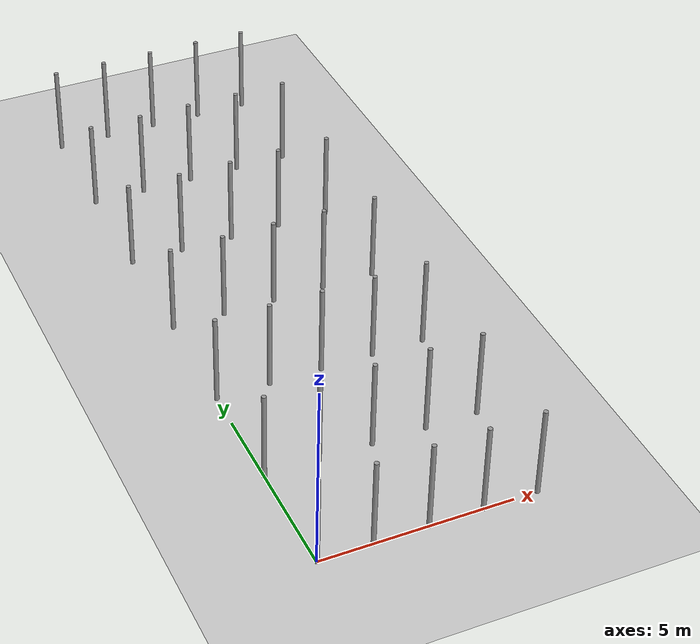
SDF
<sdf version="1.6">
 <world name="default">
  <light name="sun" type="directional">
   <pose>0 0 10 0 -0 0</pose>
   <diffuse>0.8 0.8 0.8 1</diffuse>
   <specular>0.1 0.1 0.1 1</specular>
   <attenuation>
    <range>1000</range>
    <constant>0.9</constant>
    <linear>0.01</linear>
    <quadratic>0.001</quadratic>
   </attenuation>
   <direction>-0.5 0.5 -1</direction>
  </light>
  <model name="ground_plane">
   <static>1</static>
   <link name="link">
    <collision name="collision">
     <geometry><plane><normal>0 0 1</normal><size>100 100</size></plane></geometry>
     <surface><friction><ode><mu>100</mu><mu2>50</mu2></ode></friction></surface>
    </collision>
    <visual name="visual">
     <cast_shadows>0</cast_shadows>
     <geometry><plane><normal>0 0 1</normal><size>100 100</size></plane></geometry>
     <material>
      <script><uri>file://media/materials/scripts/gazebo.material</uri><name>Gazebo/Grey</name></script>
     </material>
    </visual>
   </link>
  </model>
  <gravity>0 0 -9.8</gravity>
  <magnetic_field>6e-06 2.3e-05 -4.2e-05</magnetic_field>
  <atmosphere type="adiabatic"/>
  <physics name="default_physics" default="0" type="ode">
   <max_step_size>0.001</max_step_size>
   <real_time_factor>1</real_time_factor>
   <real_time_update_rate>1000</real_time_update_rate>
  </physics>
  <scene><ambient>0.4 0.4 0.4 1</ambient><background>0.7 0.7 0.7 1</background><shadows>1</shadows></scene>
  <spherical_coordinates>
   <surface_model>EARTH_WGS84</surface_model>
   <latitude_deg>0</latitude_deg>
   <longitude_deg>0</longitude_deg>
   <elevation>0</elevation>
   <heading_deg>0</heading_deg>
  </spherical_coordinates>
  <model name="pole_8">
   <link name="link_0">
    <inertial>
     <mass>0.0364582</mass>
     <inertia>
      <ixx>0.00312124</ixx>
      <ixy>0</ixy>
      <ixz>0</ixz>
      <iyy>0.00312124</iyy>
      <iyz>0</iyz>
      <izz>0.00016615</izz>
     </inertia>
    </inertial>
    <visual name="visual">
     <geometry><cylinder><radius>0.06</radius><length>2.5</length></cylinder></geometry>
     <material>
      <lighting>1</lighting>
      <script><uri>file://media/materials/scripts/gazebo.material</uri><name>Gazebo/Grey</name></script>
      <ambient>0.3 0.3 0.3 1</ambient>
      <diffuse>0.7 0.7 0.7 1</diffuse>
      <specular>0.01 0.01 0.01 1</specular>
      <emissive>0 0 0 1</emissive>
      <shader type="vertex"><normal_map>__default__</normal_map></shader>
     </material>
    </visual>
    <collision name="collision">
     <geometry><cylinder><radius>0.06</radius><length>2.5</length></cylinder></geometry>
     <surface>
      <friction>
       <ode><mu>1</mu><mu2>1</mu2><fdir1>0 0 0</fdir1><slip1>0</slip1><slip2>0</slip2></ode>
       <torsional>
        <coefficient>1</coefficient>
        <patch_radius>0</patch_radius>
        <surface_radius>0</surface_radius>
        <use_patch_radius>1</use_patch_radius>
        <ode><slip>0</slip></ode>
       </torsional>
      </friction>
      <bounce><restitution_coefficient>0</restitution_coefficient><threshold>1e+06</threshold></bounce>
      <contact>
       <collide_without_contact>0</collide_without_contact>
       <collide_without_contact_bitmask>1</collide_without_contact_bitmask>
       <collide_bitmask>1</collide_bitmask>
       <ode>
        <soft_cfm>0</soft_cfm>
        <soft_erp>0.2</soft_erp>
        <kp>1e+13</kp>
        <kd>1</kd>
        <max_vel>0.01</max_vel>
        <min_depth>0</min_depth>
       </ode>
       <bullet>
        <split_impulse>1</split_impulse>
        <split_impulse_penetration_threshold>-0.01</split_impulse_penetration_threshold>
        <soft_cfm>0</soft_cfm>
        <soft_erp>0.2</soft_erp>
        <kp>1e+13</kp>
        <kd>1</kd>
       </bullet>
      </contact>
     </surface>
    </collision>
   </link>
   <static>0</static>
   <pose>1.40425 0.001634 1.24999 -1e-06 -0 -0.021184</pose>
  </model>
  <model name="pole_9">
   <link name="link_0">
    <inertial>
     <mass>0.0364582</mass>
     <inertia>
      <ixx>0.00312124</ixx>
      <ixy>0</ixy>
      <ixz>0</ixz>
      <iyy>0.00312124</iyy>
      <iyz>0</iyz>
      <izz>0.00016615</izz>
     </inertia>
    </inertial>
    <visual name="visual">
     <geometry><cylinder><radius>0.06</radius><length>2.5</length></cylinder></geometry>
     <material>
      <lighting>1</lighting>
      <script><uri>file://media/materials/scripts/gazebo.material</uri><name>Gazebo/Grey</name></script>
      <ambient>0.3 0.3 0.3 1</ambient>
      <diffuse>0.7 0.7 0.7 1</diffuse>
      <specular>0.01 0.01 0.01 1</specular>
      <emissive>0 0 0 1</emissive>
      <shader type="vertex"><normal_map>__default__</normal_map></shader>
     </material>
    </visual>
    <collision name="collision">
     <geometry><cylinder><radius>0.06</radius><length>2.5</length></cylinder></geometry>
     <surface>
      <friction>
       <ode><mu>1</mu><mu2>1</mu2><fdir1>0 0 0</fdir1><slip1>0</slip1><slip2>0</slip2></ode>
       <torsional>
        <coefficient>1</coefficient>
        <patch_radius>0</patch_radius>
        <surface_radius>0</surface_radius>
        <use_patch_radius>1</use_patch_radius>
        <ode><slip>0</slip></ode>
       </torsional>
      </friction>
      <bounce><restitution_coefficient>0</restitution_coefficient><threshold>1e+06</threshold></bounce>
      <contact>
       <collide_without_contact>0</collide_without_contact>
       <collide_without_contact_bitmask>1</collide_without_contact_bitmask>
       <collide_bitmask>1</collide_bitmask>
       <ode>
        <soft_cfm>0</soft_cfm>
        <soft_erp>0.2</soft_erp>
        <kp>1e+13</kp>
        <kd>1</kd>
        <max_vel>0.01</max_vel>
        <min_depth>0</min_depth>
       </ode>
       <bullet>
        <split_impulse>1</split_impulse>
        <split_impulse_penetration_threshold>-0.01</split_impulse_penetration_threshold>
        <soft_cfm>0</soft_cfm>
        <soft_erp>0.2</soft_erp>
        <kp>1e+13</kp>
        <kd>1</kd>
       </bullet>
      </contact>
     </surface>
    </collision>
   </link>
   <static>0</static>
   <pose>2.80805 0.00187 1.24999 0 1e-06 -0.038737</pose>
  </model>
  <model name="pole_10">
   <link name="link_0">
    <inertial>
     <mass>0.0364582</mass>
     <inertia>
      <ixx>0.00312124</ixx>
      <ixy>0</ixy>
      <ixz>0</ixz>
      <iyy>0.00312124</iyy>
      <iyz>0</iyz>
      <izz>0.00016615</izz>
     </inertia>
    </inertial>
    <visual name="visual">
     <geometry><cylinder><radius>0.06</radius><length>2.5</length></cylinder></geometry>
     <material>
      <lighting>1</lighting>
      <script><uri>file://media/materials/scripts/gazebo.material</uri><name>Gazebo/Grey</name></script>
      <ambient>0.3 0.3 0.3 1</ambient>
      <diffuse>0.7 0.7 0.7 1</diffuse>
      <specular>0.01 0.01 0.01 1</specular>
      <emissive>0 0 0 1</emissive>
      <shader type="vertex"><normal_map>__default__</normal_map></shader>
     </material>
    </visual>
    <collision name="collision">
     <geometry><cylinder><radius>0.06</radius><length>2.5</length></cylinder></geometry>
     <surface>
      <friction>
       <ode><mu>1</mu><mu2>1</mu2><fdir1>0 0 0</fdir1><slip1>0</slip1><slip2>0</slip2></ode>
       <torsional>
        <coefficient>1</coefficient>
        <patch_radius>0</patch_radius>
        <surface_radius>0</surface_radius>
        <use_patch_radius>1</use_patch_radius>
        <ode><slip>0</slip></ode>
       </torsional>
      </friction>
      <bounce><restitution_coefficient>0</restitution_coefficient><threshold>1e+06</threshold></bounce>
      <contact>
       <collide_without_contact>0</collide_without_contact>
       <collide_without_contact_bitmask>1</collide_without_contact_bitmask>
       <collide_bitmask>1</collide_bitmask>
       <ode>
        <soft_cfm>0</soft_cfm>
        <soft_erp>0.2</soft_erp>
        <kp>1e+13</kp>
        <kd>1</kd>
        <max_vel>0.01</max_vel>
        <min_depth>0</min_depth>
       </ode>
       <bullet>
        <split_impulse>1</split_impulse>
        <split_impulse_penetration_threshold>-0.01</split_impulse_penetration_threshold>
        <soft_cfm>0</soft_cfm>
        <soft_erp>0.2</soft_erp>
        <kp>1e+13</kp>
        <kd>1</kd>
       </bullet>
      </contact>
     </surface>
    </collision>
   </link>
   <static>0</static>
   <pose>4.20399 0.001699 1.24999 -1e-06 1e-06 -0.02411</pose>
  </model>
  <model name="pole_11">
   <link name="link_0">
    <inertial>
     <mass>0.0364582</mass>
     <inertia>
      <ixx>0.00312124</ixx>
      <ixy>0</ixy>
      <ixz>0</ixz>
      <iyy>0.00312124</iyy>
      <iyz>0</iyz>
      <izz>0.00016615</izz>
     </inertia>
    </inertial>
    <visual name="visual">
     <geometry><cylinder><radius>0.06</radius><length>2.5</length></cylinder></geometry>
     <material>
      <lighting>1</lighting>
      <script><uri>file://media/materials/scripts/gazebo.material</uri><name>Gazebo/Grey</name></script>
      <ambient>0.3 0.3 0.3 1</ambient>
      <diffuse>0.7 0.7 0.7 1</diffuse>
      <specular>0.01 0.01 0.01 1</specular>
      <emissive>0 0 0 1</emissive>
      <shader type="vertex"><normal_map>__default__</normal_map></shader>
     </material>
    </visual>
    <collision name="collision">
     <geometry><cylinder><radius>0.06</radius><length>2.5</length></cylinder></geometry>
     <surface>
      <friction>
       <ode><mu>1</mu><mu2>1</mu2><fdir1>0 0 0</fdir1><slip1>0</slip1><slip2>0</slip2></ode>
       <torsional>
        <coefficient>1</coefficient>
        <patch_radius>0</patch_radius>
        <surface_radius>0</surface_radius>
        <use_patch_radius>1</use_patch_radius>
        <ode><slip>0</slip></ode>
       </torsional>
      </friction>
      <bounce><restitution_coefficient>0</restitution_coefficient><threshold>1e+06</threshold></bounce>
      <contact>
       <collide_without_contact>0</collide_without_contact>
       <collide_without_contact_bitmask>1</collide_without_contact_bitmask>
       <collide_bitmask>1</collide_bitmask>
       <ode>
        <soft_cfm>0</soft_cfm>
        <soft_erp>0.2</soft_erp>
        <kp>1e+13</kp>
        <kd>1</kd>
        <max_vel>0.01</max_vel>
        <min_depth>0</min_depth>
       </ode>
       <bullet>
        <split_impulse>1</split_impulse>
        <split_impulse_penetration_threshold>-0.01</split_impulse_penetration_threshold>
        <soft_cfm>0</soft_cfm>
        <soft_erp>0.2</soft_erp>
        <kp>1e+13</kp>
        <kd>1</kd>
       </bullet>
      </contact>
     </surface>
    </collision>
   </link>
   <static>0</static>
   <pose>5.61625 0.00135 1.24999 -1e-06 1e-06 -0.021959</pose>
  </model>
  <model name="pole_11_clone">
   <link name="link_0">
    <inertial>
     <mass>0.0364582</mass>
     <inertia>
      <ixx>0.00312124</ixx>
      <ixy>0</ixy>
      <ixz>0</ixz>
      <iyy>0.00312124</iyy>
      <iyz>0</iyz>
      <izz>0.00016615</izz>
     </inertia>
    </inertial>
    <visual name="visual">
     <geometry><cylinder><radius>0.06</radius><length>2.5</length></cylinder></geometry>
     <material>
      <lighting>1</lighting>
      <script><uri>file://media/materials/scripts/gazebo.material</uri><name>Gazebo/Grey</name></script>
      <ambient>0.3 0.3 0.3 1</ambient>
      <diffuse>0.7 0.7 0.7 1</diffuse>
      <specular>0.01 0.01 0.01 1</specular>
      <emissive>0 0 0 1</emissive>
      <shader type="vertex"><normal_map>__default__</normal_map></shader>
     </material>
    </visual>
    <collision name="collision">
     <geometry><cylinder><radius>0.06</radius><length>2.5</length></cylinder></geometry>
     <surface>
      <friction>
       <ode><mu>1</mu><mu2>1</mu2><fdir1>0 0 0</fdir1><slip1>0</slip1><slip2>0</slip2></ode>
       <torsional>
        <coefficient>1</coefficient>
        <patch_radius>0</patch_radius>
        <surface_radius>0</surface_radius>
        <use_patch_radius>1</use_patch_radius>
        <ode><slip>0</slip></ode>
       </torsional>
      </friction>
      <bounce><restitution_coefficient>0</restitution_coefficient><threshold>1e+06</threshold></bounce>
      <contact>
       <collide_without_contact>0</collide_without_contact>
       <collide_without_contact_bitmask>1</collide_without_contact_bitmask>
       <collide_bitmask>1</collide_bitmask>
       <ode>
        <soft_cfm>0</soft_cfm>
        <soft_erp>0.2</soft_erp>
        <kp>1e+13</kp>
        <kd>1</kd>
        <max_vel>0.01</max_vel>
        <min_depth>0</min_depth>
       </ode>
       <bullet>
        <split_impulse>1</split_impulse>
        <split_impulse_penetration_threshold>-0.01</split_impulse_penetration_threshold>
        <soft_cfm>0</soft_cfm>
        <soft_erp>0.2</soft_erp>
        <kp>1e+13</kp>
        <kd>1</kd>
       </bullet>
      </contact>
     </surface>
    </collision>
   </link>
   <static>0</static>
   <pose>0.000263 2.98169 1.25 -1e-06 -1e-06 -0.021983</pose>
  </model>
  <model name="pole">
   <link name="link_0">
    <inertial>
     <mass>0.0364582</mass>
     <inertia>
      <ixx>0.00312124</ixx>
      <ixy>0</ixy>
      <ixz>0</ixz>
      <iyy>0.00312124</iyy>
      <iyz>0</iyz>
      <izz>0.00016615</izz>
     </inertia>
    </inertial>
    <visual name="visual">
     <geometry><cylinder><radius>0.06</radius><length>2.5</length></cylinder></geometry>
     <material>
      <lighting>1</lighting>
      <script><uri>file://media/materials/scripts/gazebo.material</uri><name>Gazebo/Grey</name></script>
      <ambient>0.3 0.3 0.3 1</ambient>
      <diffuse>0.7 0.7 0.7 1</diffuse>
      <specular>0.01 0.01 0.01 1</specular>
      <emissive>0 0 0 1</emissive>
      <shader type="vertex"><normal_map>__default__</normal_map></shader>
     </material>
    </visual>
    <collision name="collision">
     <geometry><cylinder><radius>0.06</radius><length>2.5</length></cylinder></geometry>
     <surface>
      <friction>
       <ode><mu>1</mu><mu2>1</mu2><fdir1>0 0 0</fdir1><slip1>0</slip1><slip2>0</slip2></ode>
       <torsional>
        <coefficient>1</coefficient>
        <patch_radius>0</patch_radius>
        <surface_radius>0</surface_radius>
        <use_patch_radius>1</use_patch_radius>
        <ode><slip>0</slip></ode>
       </torsional>
      </friction>
      <bounce><restitution_coefficient>0</restitution_coefficient><threshold>1e+06</threshold></bounce>
      <contact>
       <collide_without_contact>0</collide_without_contact>
       <collide_without_contact_bitmask>1</collide_without_contact_bitmask>
       <collide_bitmask>1</collide_bitmask>
       <ode>
        <soft_cfm>0</soft_cfm>
        <soft_erp>0.2</soft_erp>
        <kp>1e+13</kp>
        <kd>1</kd>
        <max_vel>0.01</max_vel>
        <min_depth>0</min_depth>
       </ode>
       <bullet>
        <split_impulse>1</split_impulse>
        <split_impulse_penetration_threshold>-0.01</split_impulse_penetration_threshold>
        <soft_cfm>0</soft_cfm>
        <soft_erp>0.2</soft_erp>
        <kp>1e+13</kp>
        <kd>1</kd>
       </bullet>
      </contact>
     </surface>
    </collision>
   </link>
   <static>0</static>
   <pose>0.006721 5.96143 1.25 -1e-06 0 -0.017473</pose>
  </model>
  <model name="pole_0">
   <link name="link_0">
    <inertial>
     <mass>0.0364582</mass>
     <inertia>
      <ixx>0.00312124</ixx>
      <ixy>0</ixy>
      <ixz>0</ixz>
      <iyy>0.00312124</iyy>
      <iyz>0</iyz>
      <izz>0.00016615</izz>
     </inertia>
    </inertial>
    <visual name="visual">
     <geometry><cylinder><radius>0.06</radius><length>2.5</length></cylinder></geometry>
     <material>
      <lighting>1</lighting>
      <script><uri>file://media/materials/scripts/gazebo.material</uri><name>Gazebo/Grey</name></script>
      <ambient>0.3 0.3 0.3 1</ambient>
      <diffuse>0.7 0.7 0.7 1</diffuse>
      <specular>0.01 0.01 0.01 1</specular>
      <emissive>0 0 0 1</emissive>
      <shader type="vertex"><normal_map>__default__</normal_map></shader>
     </material>
    </visual>
    <collision name="collision">
     <geometry><cylinder><radius>0.06</radius><length>2.5</length></cylinder></geometry>
     <surface>
      <friction>
       <ode><mu>1</mu><mu2>1</mu2><fdir1>0 0 0</fdir1><slip1>0</slip1><slip2>0</slip2></ode>
       <torsional>
        <coefficient>1</coefficient>
        <patch_radius>0</patch_radius>
        <surface_radius>0</surface_radius>
        <use_patch_radius>1</use_patch_radius>
        <ode><slip>0</slip></ode>
       </torsional>
      </friction>
      <bounce><restitution_coefficient>0</restitution_coefficient><threshold>1e+06</threshold></bounce>
      <contact>
       <collide_without_contact>0</collide_without_contact>
       <collide_without_contact_bitmask>1</collide_without_contact_bitmask>
       <collide_bitmask>1</collide_bitmask>
       <ode>
        <soft_cfm>0</soft_cfm>
        <soft_erp>0.2</soft_erp>
        <kp>1e+13</kp>
        <kd>1</kd>
        <max_vel>0.01</max_vel>
        <min_depth>0</min_depth>
       </ode>
       <bullet>
        <split_impulse>1</split_impulse>
        <split_impulse_penetration_threshold>-0.01</split_impulse_penetration_threshold>
        <soft_cfm>0</soft_cfm>
        <soft_erp>0.2</soft_erp>
        <kp>1e+13</kp>
        <kd>1</kd>
       </bullet>
      </contact>
     </surface>
    </collision>
   </link>
   <static>0</static>
   <pose>0.013539 8.94158 1.25 -0 1e-06 -0.02062</pose>
  </model>
  <model name="pole_1">
   <link name="link_0">
    <inertial>
     <mass>0.0364582</mass>
     <inertia>
      <ixx>0.00312124</ixx>
      <ixy>0</ixy>
      <ixz>0</ixz>
      <iyy>0.00312124</iyy>
      <iyz>0</iyz>
      <izz>0.00016615</izz>
     </inertia>
    </inertial>
    <visual name="visual">
     <geometry><cylinder><radius>0.06</radius><length>2.5</length></cylinder></geometry>
     <material>
      <lighting>1</lighting>
      <script><uri>file://media/materials/scripts/gazebo.material</uri><name>Gazebo/Grey</name></script>
      <ambient>0.3 0.3 0.3 1</ambient>
      <diffuse>0.7 0.7 0.7 1</diffuse>
      <specular>0.01 0.01 0.01 1</specular>
      <emissive>0 0 0 1</emissive>
      <shader type="vertex"><normal_map>__default__</normal_map></shader>
     </material>
    </visual>
    <collision name="collision">
     <geometry><cylinder><radius>0.06</radius><length>2.5</length></cylinder></geometry>
     <surface>
      <friction>
       <ode><mu>1</mu><mu2>1</mu2><fdir1>0 0 0</fdir1><slip1>0</slip1><slip2>0</slip2></ode>
       <torsional>
        <coefficient>1</coefficient>
        <patch_radius>0</patch_radius>
        <surface_radius>0</surface_radius>
        <use_patch_radius>1</use_patch_radius>
        <ode><slip>0</slip></ode>
       </torsional>
      </friction>
      <bounce><restitution_coefficient>0</restitution_coefficient><threshold>1e+06</threshold></bounce>
      <contact>
       <collide_without_contact>0</collide_without_contact>
       <collide_without_contact_bitmask>1</collide_without_contact_bitmask>
       <collide_bitmask>1</collide_bitmask>
       <ode>
        <soft_cfm>0</soft_cfm>
        <soft_erp>0.2</soft_erp>
        <kp>1e+13</kp>
        <kd>1</kd>
        <max_vel>0.01</max_vel>
        <min_depth>0</min_depth>
       </ode>
       <bullet>
        <split_impulse>1</split_impulse>
        <split_impulse_penetration_threshold>-0.01</split_impulse_penetration_threshold>
        <soft_cfm>0</soft_cfm>
        <soft_erp>0.2</soft_erp>
        <kp>1e+13</kp>
        <kd>1</kd>
       </bullet>
      </contact>
     </surface>
    </collision>
   </link>
   <static>0</static>
   <pose>-0.008088 11.9215 1.25 -0 1e-06 -0.020103</pose>
  </model>
  <model name="pole_2">
   <link name="link_0">
    <inertial>
     <mass>0.0364582</mass>
     <inertia>
      <ixx>0.00312124</ixx>
      <ixy>0</ixy>
      <ixz>0</ixz>
      <iyy>0.00312124</iyy>
      <iyz>0</iyz>
      <izz>0.00016615</izz>
     </inertia>
    </inertial>
    <visual name="visual">
     <geometry><cylinder><radius>0.06</radius><length>2.5</length></cylinder></geometry>
     <material>
      <lighting>1</lighting>
      <script><uri>file://media/materials/scripts/gazebo.material</uri><name>Gazebo/Grey</name></script>
      <ambient>0.3 0.3 0.3 1</ambient>
      <diffuse>0.7 0.7 0.7 1</diffuse>
      <specular>0.01 0.01 0.01 1</specular>
      <emissive>0 0 0 1</emissive>
      <shader type="vertex"><normal_map>__default__</normal_map></shader>
     </material>
    </visual>
    <collision name="collision">
     <geometry><cylinder><radius>0.06</radius><length>2.5</length></cylinder></geometry>
     <surface>
      <friction>
       <ode><mu>1</mu><mu2>1</mu2><fdir1>0 0 0</fdir1><slip1>0</slip1><slip2>0</slip2></ode>
       <torsional>
        <coefficient>1</coefficient>
        <patch_radius>0</patch_radius>
        <surface_radius>0</surface_radius>
        <use_patch_radius>1</use_patch_radius>
        <ode><slip>0</slip></ode>
       </torsional>
      </friction>
      <bounce><restitution_coefficient>0</restitution_coefficient><threshold>1e+06</threshold></bounce>
      <contact>
       <collide_without_contact>0</collide_without_contact>
       <collide_without_contact_bitmask>1</collide_without_contact_bitmask>
       <collide_bitmask>1</collide_bitmask>
       <ode>
        <soft_cfm>0</soft_cfm>
        <soft_erp>0.2</soft_erp>
        <kp>1e+13</kp>
        <kd>1</kd>
        <max_vel>0.01</max_vel>
        <min_depth>0</min_depth>
       </ode>
       <bullet>
        <split_impulse>1</split_impulse>
        <split_impulse_penetration_threshold>-0.01</split_impulse_penetration_threshold>
        <soft_cfm>0</soft_cfm>
        <soft_erp>0.2</soft_erp>
        <kp>1e+13</kp>
        <kd>1</kd>
       </bullet>
      </contact>
     </surface>
    </collision>
   </link>
   <static>0</static>
   <pose>2.1e-05 14.8944 1.24999 0 -1e-06 0.217518</pose>
  </model>
  <model name="pole_3">
   <link name="link_0">
    <inertial>
     <mass>0.0364582</mass>
     <inertia>
      <ixx>0.00312124</ixx>
      <ixy>0</ixy>
      <ixz>0</ixz>
      <iyy>0.00312124</iyy>
      <iyz>0</iyz>
      <izz>0.00016615</izz>
     </inertia>
    </inertial>
    <visual name="visual">
     <geometry><cylinder><radius>0.06</radius><length>2.5</length></cylinder></geometry>
     <material>
      <lighting>1</lighting>
      <script><uri>file://media/materials/scripts/gazebo.material</uri><name>Gazebo/Grey</name></script>
      <ambient>0.3 0.3 0.3 1</ambient>
      <diffuse>0.7 0.7 0.7 1</diffuse>
      <specular>0.01 0.01 0.01 1</specular>
      <emissive>0 0 0 1</emissive>
      <shader type="vertex"><normal_map>__default__</normal_map></shader>
     </material>
    </visual>
    <collision name="collision">
     <geometry><cylinder><radius>0.06</radius><length>2.5</length></cylinder></geometry>
     <surface>
      <friction>
       <ode><mu>1</mu><mu2>1</mu2><fdir1>0 0 0</fdir1><slip1>0</slip1><slip2>0</slip2></ode>
       <torsional>
        <coefficient>1</coefficient>
        <patch_radius>0</patch_radius>
        <surface_radius>0</surface_radius>
        <use_patch_radius>1</use_patch_radius>
        <ode><slip>0</slip></ode>
       </torsional>
      </friction>
      <bounce><restitution_coefficient>0</restitution_coefficient><threshold>1e+06</threshold></bounce>
      <contact>
       <collide_without_contact>0</collide_without_contact>
       <collide_without_contact_bitmask>1</collide_without_contact_bitmask>
       <collide_bitmask>1</collide_bitmask>
       <ode>
        <soft_cfm>0</soft_cfm>
        <soft_erp>0.2</soft_erp>
        <kp>1e+13</kp>
        <kd>1</kd>
        <max_vel>0.01</max_vel>
        <min_depth>0</min_depth>
       </ode>
       <bullet>
        <split_impulse>1</split_impulse>
        <split_impulse_penetration_threshold>-0.01</split_impulse_penetration_threshold>
        <soft_cfm>0</soft_cfm>
        <soft_erp>0.2</soft_erp>
        <kp>1e+13</kp>
        <kd>1</kd>
       </bullet>
      </contact>
     </surface>
    </collision>
   </link>
   <static>0</static>
   <pose>1.40475 2.98129 1.25 -1e-06 -0 -0.016085</pose>
  </model>
  <model name="pole_5">
   <link name="link_0">
    <inertial>
     <mass>0.0364582</mass>
     <inertia>
      <ixx>0.00312124</ixx>
      <ixy>0</ixy>
      <ixz>0</ixz>
      <iyy>0.00312124</iyy>
      <iyz>0</iyz>
      <izz>0.00016615</izz>
     </inertia>
    </inertial>
    <visual name="visual">
     <geometry><cylinder><radius>0.06</radius><length>2.5</length></cylinder></geometry>
     <material>
      <lighting>1</lighting>
      <script><uri>file://media/materials/scripts/gazebo.material</uri><name>Gazebo/Grey</name></script>
      <ambient>0.3 0.3 0.3 1</ambient>
      <diffuse>0.7 0.7 0.7 1</diffuse>
      <specular>0.01 0.01 0.01 1</specular>
      <emissive>0 0 0 1</emissive>
      <shader type="vertex"><normal_map>__default__</normal_map></shader>
     </material>
    </visual>
    <collision name="collision">
     <geometry><cylinder><radius>0.06</radius><length>2.5</length></cylinder></geometry>
     <surface>
      <friction>
       <ode><mu>1</mu><mu2>1</mu2><fdir1>0 0 0</fdir1><slip1>0</slip1><slip2>0</slip2></ode>
       <torsional>
        <coefficient>1</coefficient>
        <patch_radius>0</patch_radius>
        <surface_radius>0</surface_radius>
        <use_patch_radius>1</use_patch_radius>
        <ode><slip>0</slip></ode>
       </torsional>
      </friction>
      <bounce><restitution_coefficient>0</restitution_coefficient><threshold>1e+06</threshold></bounce>
      <contact>
       <collide_without_contact>0</collide_without_contact>
       <collide_without_contact_bitmask>1</collide_without_contact_bitmask>
       <collide_bitmask>1</collide_bitmask>
       <ode>
        <soft_cfm>0</soft_cfm>
        <soft_erp>0.2</soft_erp>
        <kp>1e+13</kp>
        <kd>1</kd>
        <max_vel>0.01</max_vel>
        <min_depth>0</min_depth>
       </ode>
       <bullet>
        <split_impulse>1</split_impulse>
        <split_impulse_penetration_threshold>-0.01</split_impulse_penetration_threshold>
        <soft_cfm>0</soft_cfm>
        <soft_erp>0.2</soft_erp>
        <kp>1e+13</kp>
        <kd>1</kd>
       </bullet>
      </contact>
     </surface>
    </collision>
   </link>
   <static>0</static>
   <pose>2.79582 2.98123 1.24999 1e-06 2e-06 -0.014139</pose>
  </model>
  <model name="pole_6">
   <link name="link_0">
    <inertial>
     <mass>0.0364582</mass>
     <inertia>
      <ixx>0.00312124</ixx>
      <ixy>0</ixy>
      <ixz>0</ixz>
      <iyy>0.00312124</iyy>
      <iyz>0</iyz>
      <izz>0.00016615</izz>
     </inertia>
    </inertial>
    <visual name="visual">
     <geometry><cylinder><radius>0.06</radius><length>2.5</length></cylinder></geometry>
     <material>
      <lighting>1</lighting>
      <script><uri>file://media/materials/scripts/gazebo.material</uri><name>Gazebo/Grey</name></script>
      <ambient>0.3 0.3 0.3 1</ambient>
      <diffuse>0.7 0.7 0.7 1</diffuse>
      <specular>0.01 0.01 0.01 1</specular>
      <emissive>0 0 0 1</emissive>
      <shader type="vertex"><normal_map>__default__</normal_map></shader>
     </material>
    </visual>
    <collision name="collision">
     <geometry><cylinder><radius>0.06</radius><length>2.5</length></cylinder></geometry>
     <surface>
      <friction>
       <ode><mu>1</mu><mu2>1</mu2><fdir1>0 0 0</fdir1><slip1>0</slip1><slip2>0</slip2></ode>
       <torsional>
        <coefficient>1</coefficient>
        <patch_radius>0</patch_radius>
        <surface_radius>0</surface_radius>
        <use_patch_radius>1</use_patch_radius>
        <ode><slip>0</slip></ode>
       </torsional>
      </friction>
      <bounce><restitution_coefficient>0</restitution_coefficient><threshold>1e+06</threshold></bounce>
      <contact>
       <collide_without_contact>0</collide_without_contact>
       <collide_without_contact_bitmask>1</collide_without_contact_bitmask>
       <collide_bitmask>1</collide_bitmask>
       <ode>
        <soft_cfm>0</soft_cfm>
        <soft_erp>0.2</soft_erp>
        <kp>1e+13</kp>
        <kd>1</kd>
        <max_vel>0.01</max_vel>
        <min_depth>0</min_depth>
       </ode>
       <bullet>
        <split_impulse>1</split_impulse>
        <split_impulse_penetration_threshold>-0.01</split_impulse_penetration_threshold>
        <soft_cfm>0</soft_cfm>
        <soft_erp>0.2</soft_erp>
        <kp>1e+13</kp>
        <kd>1</kd>
       </bullet>
      </contact>
     </surface>
    </collision>
   </link>
   <static>0</static>
   <pose>4.22242 2.98137 1.24999 0 -2e-06 -0.015298</pose>
  </model>
  <model name="pole_7">
   <link name="link_0">
    <inertial>
     <mass>0.0364582</mass>
     <inertia>
      <ixx>0.00312124</ixx>
      <ixy>0</ixy>
      <ixz>0</ixz>
      <iyy>0.00312124</iyy>
      <iyz>0</iyz>
      <izz>0.00016615</izz>
     </inertia>
    </inertial>
    <visual name="visual">
     <geometry><cylinder><radius>0.06</radius><length>2.5</length></cylinder></geometry>
     <material>
      <lighting>1</lighting>
      <script><uri>file://media/materials/scripts/gazebo.material</uri><name>Gazebo/Grey</name></script>
      <ambient>0.3 0.3 0.3 1</ambient>
      <diffuse>0.7 0.7 0.7 1</diffuse>
      <specular>0.01 0.01 0.01 1</specular>
      <emissive>0 0 0 1</emissive>
      <shader type="vertex"><normal_map>__default__</normal_map></shader>
     </material>
    </visual>
    <collision name="collision">
     <geometry><cylinder><radius>0.06</radius><length>2.5</length></cylinder></geometry>
     <surface>
      <friction>
       <ode><mu>1</mu><mu2>1</mu2><fdir1>0 0 0</fdir1><slip1>0</slip1><slip2>0</slip2></ode>
       <torsional>
        <coefficient>1</coefficient>
        <patch_radius>0</patch_radius>
        <surface_radius>0</surface_radius>
        <use_patch_radius>1</use_patch_radius>
        <ode><slip>0</slip></ode>
       </torsional>
      </friction>
      <bounce><restitution_coefficient>0</restitution_coefficient><threshold>1e+06</threshold></bounce>
      <contact>
       <collide_without_contact>0</collide_without_contact>
       <collide_without_contact_bitmask>1</collide_without_contact_bitmask>
       <collide_bitmask>1</collide_bitmask>
       <ode>
        <soft_cfm>0</soft_cfm>
        <soft_erp>0.2</soft_erp>
        <kp>1e+13</kp>
        <kd>1</kd>
        <max_vel>0.01</max_vel>
        <min_depth>0</min_depth>
       </ode>
       <bullet>
        <split_impulse>1</split_impulse>
        <split_impulse_penetration_threshold>-0.01</split_impulse_penetration_threshold>
        <soft_cfm>0</soft_cfm>
        <soft_erp>0.2</soft_erp>
        <kp>1e+13</kp>
        <kd>1</kd>
       </bullet>
      </contact>
     </surface>
    </collision>
   </link>
   <static>0</static>
   <pose>5.60735 2.98129 1.25 0 -1e-06 -0.014591</pose>
  </model>
  <model name="pole_12">
   <link name="link_0">
    <inertial>
     <mass>0.0364582</mass>
     <inertia>
      <ixx>0.00312124</ixx>
      <ixy>0</ixy>
      <ixz>0</ixz>
      <iyy>0.00312124</iyy>
      <iyz>0</iyz>
      <izz>0.00016615</izz>
     </inertia>
    </inertial>
    <visual name="visual">
     <geometry><cylinder><radius>0.06</radius><length>2.5</length></cylinder></geometry>
     <material>
      <lighting>1</lighting>
      <script><uri>file://media/materials/scripts/gazebo.material</uri><name>Gazebo/Grey</name></script>
      <ambient>0.3 0.3 0.3 1</ambient>
      <diffuse>0.7 0.7 0.7 1</diffuse>
      <specular>0.01 0.01 0.01 1</specular>
      <emissive>0 0 0 1</emissive>
      <shader type="vertex"><normal_map>__default__</normal_map></shader>
     </material>
    </visual>
    <collision name="collision">
     <geometry><cylinder><radius>0.06</radius><length>2.5</length></cylinder></geometry>
     <surface>
      <friction>
       <ode><mu>1</mu><mu2>1</mu2><fdir1>0 0 0</fdir1><slip1>0</slip1><slip2>0</slip2></ode>
       <torsional>
        <coefficient>1</coefficient>
        <patch_radius>0</patch_radius>
        <surface_radius>0</surface_radius>
        <use_patch_radius>1</use_patch_radius>
        <ode><slip>0</slip></ode>
       </torsional>
      </friction>
      <bounce><restitution_coefficient>0</restitution_coefficient><threshold>1e+06</threshold></bounce>
      <contact>
       <collide_without_contact>0</collide_without_contact>
       <collide_without_contact_bitmask>1</collide_without_contact_bitmask>
       <collide_bitmask>1</collide_bitmask>
       <ode>
        <soft_cfm>0</soft_cfm>
        <soft_erp>0.2</soft_erp>
        <kp>1e+13</kp>
        <kd>1</kd>
        <max_vel>0.01</max_vel>
        <min_depth>0</min_depth>
       </ode>
       <bullet>
        <split_impulse>1</split_impulse>
        <split_impulse_penetration_threshold>-0.01</split_impulse_penetration_threshold>
        <soft_cfm>0</soft_cfm>
        <soft_erp>0.2</soft_erp>
        <kp>1e+13</kp>
        <kd>1</kd>
       </bullet>
      </contact>
     </surface>
    </collision>
   </link>
   <static>0</static>
   <pose>1.41362 5.96126 1.24999 -0 1e-06 -0.012678</pose>
  </model>
  <model name="pole_13">
   <link name="link_0">
    <inertial>
     <mass>0.0364582</mass>
     <inertia>
      <ixx>0.00312124</ixx>
      <ixy>0</ixy>
      <ixz>0</ixz>
      <iyy>0.00312124</iyy>
      <iyz>0</iyz>
      <izz>0.00016615</izz>
     </inertia>
    </inertial>
    <visual name="visual">
     <geometry><cylinder><radius>0.06</radius><length>2.5</length></cylinder></geometry>
     <material>
      <lighting>1</lighting>
      <script><uri>file://media/materials/scripts/gazebo.material</uri><name>Gazebo/Grey</name></script>
      <ambient>0.3 0.3 0.3 1</ambient>
      <diffuse>0.7 0.7 0.7 1</diffuse>
      <specular>0.01 0.01 0.01 1</specular>
      <emissive>0 0 0 1</emissive>
      <shader type="vertex"><normal_map>__default__</normal_map></shader>
     </material>
    </visual>
    <collision name="collision">
     <geometry><cylinder><radius>0.06</radius><length>2.5</length></cylinder></geometry>
     <surface>
      <friction>
       <ode><mu>1</mu><mu2>1</mu2><fdir1>0 0 0</fdir1><slip1>0</slip1><slip2>0</slip2></ode>
       <torsional>
        <coefficient>1</coefficient>
        <patch_radius>0</patch_radius>
        <surface_radius>0</surface_radius>
        <use_patch_radius>1</use_patch_radius>
        <ode><slip>0</slip></ode>
       </torsional>
      </friction>
      <bounce><restitution_coefficient>0</restitution_coefficient><threshold>1e+06</threshold></bounce>
      <contact>
       <collide_without_contact>0</collide_without_contact>
       <collide_without_contact_bitmask>1</collide_without_contact_bitmask>
       <collide_bitmask>1</collide_bitmask>
       <ode>
        <soft_cfm>0</soft_cfm>
        <soft_erp>0.2</soft_erp>
        <kp>1e+13</kp>
        <kd>1</kd>
        <max_vel>0.01</max_vel>
        <min_depth>0</min_depth>
       </ode>
       <bullet>
        <split_impulse>1</split_impulse>
        <split_impulse_penetration_threshold>-0.01</split_impulse_penetration_threshold>
        <soft_cfm>0</soft_cfm>
        <soft_erp>0.2</soft_erp>
        <kp>1e+13</kp>
        <kd>1</kd>
       </bullet>
      </contact>
     </surface>
    </collision>
   </link>
   <static>0</static>
   <pose>2.80803 5.96116 1.24999 0 2e-06 -0.012616</pose>
  </model>
  <model name="pole_14">
   <link name="link_0">
    <inertial>
     <mass>0.0364582</mass>
     <inertia>
      <ixx>0.00312124</ixx>
      <ixy>0</ixy>
      <ixz>0</ixz>
      <iyy>0.00312124</iyy>
      <iyz>0</iyz>
      <izz>0.00016615</izz>
     </inertia>
    </inertial>
    <visual name="visual">
     <geometry><cylinder><radius>0.06</radius><length>2.5</length></cylinder></geometry>
     <material>
      <lighting>1</lighting>
      <script><uri>file://media/materials/scripts/gazebo.material</uri><name>Gazebo/Grey</name></script>
      <ambient>0.3 0.3 0.3 1</ambient>
      <diffuse>0.7 0.7 0.7 1</diffuse>
      <specular>0.01 0.01 0.01 1</specular>
      <emissive>0 0 0 1</emissive>
      <shader type="vertex"><normal_map>__default__</normal_map></shader>
     </material>
    </visual>
    <collision name="collision">
     <geometry><cylinder><radius>0.06</radius><length>2.5</length></cylinder></geometry>
     <surface>
      <friction>
       <ode><mu>1</mu><mu2>1</mu2><fdir1>0 0 0</fdir1><slip1>0</slip1><slip2>0</slip2></ode>
       <torsional>
        <coefficient>1</coefficient>
        <patch_radius>0</patch_radius>
        <surface_radius>0</surface_radius>
        <use_patch_radius>1</use_patch_radius>
        <ode><slip>0</slip></ode>
       </torsional>
      </friction>
      <bounce><restitution_coefficient>0</restitution_coefficient><threshold>1e+06</threshold></bounce>
      <contact>
       <collide_without_contact>0</collide_without_contact>
       <collide_without_contact_bitmask>1</collide_without_contact_bitmask>
       <collide_bitmask>1</collide_bitmask>
       <ode>
        <soft_cfm>0</soft_cfm>
        <soft_erp>0.2</soft_erp>
        <kp>1e+13</kp>
        <kd>1</kd>
        <max_vel>0.01</max_vel>
        <min_depth>0</min_depth>
       </ode>
       <bullet>
        <split_impulse>1</split_impulse>
        <split_impulse_penetration_threshold>-0.01</split_impulse_penetration_threshold>
        <soft_cfm>0</soft_cfm>
        <soft_erp>0.2</soft_erp>
        <kp>1e+13</kp>
        <kd>1</kd>
       </bullet>
      </contact>
     </surface>
    </collision>
   </link>
   <static>0</static>
   <pose>4.21953 5.9611 1.24999 -1e-06 -4e-06 -0.011643</pose>
  </model>
  <model name="pole_15">
   <link name="link_0">
    <inertial>
     <mass>0.0364582</mass>
     <inertia>
      <ixx>0.00312124</ixx>
      <ixy>0</ixy>
      <ixz>0</ixz>
      <iyy>0.00312124</iyy>
      <iyz>0</iyz>
      <izz>0.00016615</izz>
     </inertia>
    </inertial>
    <visual name="visual">
     <geometry><cylinder><radius>0.06</radius><length>2.5</length></cylinder></geometry>
     <material>
      <lighting>1</lighting>
      <script><uri>file://media/materials/scripts/gazebo.material</uri><name>Gazebo/Grey</name></script>
      <ambient>0.3 0.3 0.3 1</ambient>
      <diffuse>0.7 0.7 0.7 1</diffuse>
      <specular>0.01 0.01 0.01 1</specular>
      <emissive>0 0 0 1</emissive>
      <shader type="vertex"><normal_map>__default__</normal_map></shader>
     </material>
    </visual>
    <collision name="collision">
     <geometry><cylinder><radius>0.06</radius><length>2.5</length></cylinder></geometry>
     <surface>
      <friction>
       <ode><mu>1</mu><mu2>1</mu2><fdir1>0 0 0</fdir1><slip1>0</slip1><slip2>0</slip2></ode>
       <torsional>
        <coefficient>1</coefficient>
        <patch_radius>0</patch_radius>
        <surface_radius>0</surface_radius>
        <use_patch_radius>1</use_patch_radius>
        <ode><slip>0</slip></ode>
       </torsional>
      </friction>
      <bounce><restitution_coefficient>0</restitution_coefficient><threshold>1e+06</threshold></bounce>
      <contact>
       <collide_without_contact>0</collide_without_contact>
       <collide_without_contact_bitmask>1</collide_without_contact_bitmask>
       <collide_bitmask>1</collide_bitmask>
       <ode>
        <soft_cfm>0</soft_cfm>
        <soft_erp>0.2</soft_erp>
        <kp>1e+13</kp>
        <kd>1</kd>
        <max_vel>0.01</max_vel>
        <min_depth>0</min_depth>
       </ode>
       <bullet>
        <split_impulse>1</split_impulse>
        <split_impulse_penetration_threshold>-0.01</split_impulse_penetration_threshold>
        <soft_cfm>0</soft_cfm>
        <soft_erp>0.2</soft_erp>
        <kp>1e+13</kp>
        <kd>1</kd>
       </bullet>
      </contact>
     </surface>
    </collision>
   </link>
   <static>0</static>
   <pose>5.62353 5.96123 1.24999 0 -1e-06 -0.012998</pose>
  </model>
  <model name="pole_16">
   <link name="link_0">
    <inertial>
     <mass>0.0364582</mass>
     <inertia>
      <ixx>0.00312124</ixx>
      <ixy>0</ixy>
      <ixz>0</ixz>
      <iyy>0.00312124</iyy>
      <iyz>0</iyz>
      <izz>0.00016615</izz>
     </inertia>
    </inertial>
    <visual name="visual">
     <geometry><cylinder><radius>0.06</radius><length>2.5</length></cylinder></geometry>
     <material>
      <lighting>1</lighting>
      <script><uri>file://media/materials/scripts/gazebo.material</uri><name>Gazebo/Grey</name></script>
      <ambient>0.3 0.3 0.3 1</ambient>
      <diffuse>0.7 0.7 0.7 1</diffuse>
      <specular>0.01 0.01 0.01 1</specular>
      <emissive>0 0 0 1</emissive>
      <shader type="vertex"><normal_map>__default__</normal_map></shader>
     </material>
    </visual>
    <collision name="collision">
     <geometry><cylinder><radius>0.06</radius><length>2.5</length></cylinder></geometry>
     <surface>
      <friction>
       <ode><mu>1</mu><mu2>1</mu2><fdir1>0 0 0</fdir1><slip1>0</slip1><slip2>0</slip2></ode>
       <torsional>
        <coefficient>1</coefficient>
        <patch_radius>0</patch_radius>
        <surface_radius>0</surface_radius>
        <use_patch_radius>1</use_patch_radius>
        <ode><slip>0</slip></ode>
       </torsional>
      </friction>
      <bounce><restitution_coefficient>0</restitution_coefficient><threshold>1e+06</threshold></bounce>
      <contact>
       <collide_without_contact>0</collide_without_contact>
       <collide_without_contact_bitmask>1</collide_without_contact_bitmask>
       <collide_bitmask>1</collide_bitmask>
       <ode>
        <soft_cfm>0</soft_cfm>
        <soft_erp>0.2</soft_erp>
        <kp>1e+13</kp>
        <kd>1</kd>
        <max_vel>0.01</max_vel>
        <min_depth>0</min_depth>
       </ode>
       <bullet>
        <split_impulse>1</split_impulse>
        <split_impulse_penetration_threshold>-0.01</split_impulse_penetration_threshold>
        <soft_cfm>0</soft_cfm>
        <soft_erp>0.2</soft_erp>
        <kp>1e+13</kp>
        <kd>1</kd>
       </bullet>
      </contact>
     </surface>
    </collision>
   </link>
   <static>0</static>
   <pose>1.41314 8.94084 1.25 0 1e-06 -0.015959</pose>
  </model>
  <model name="pole_17">
   <link name="link_0">
    <inertial>
     <mass>0.0364582</mass>
     <inertia>
      <ixx>0.00312124</ixx>
      <ixy>0</ixy>
      <ixz>0</ixz>
      <iyy>0.00312124</iyy>
      <iyz>0</iyz>
      <izz>0.00016615</izz>
     </inertia>
    </inertial>
    <visual name="visual">
     <geometry><cylinder><radius>0.06</radius><length>2.5</length></cylinder></geometry>
     <material>
      <lighting>1</lighting>
      <script><uri>file://media/materials/scripts/gazebo.material</uri><name>Gazebo/Grey</name></script>
      <ambient>0.3 0.3 0.3 1</ambient>
      <diffuse>0.7 0.7 0.7 1</diffuse>
      <specular>0.01 0.01 0.01 1</specular>
      <emissive>0 0 0 1</emissive>
      <shader type="vertex"><normal_map>__default__</normal_map></shader>
     </material>
    </visual>
    <collision name="collision">
     <geometry><cylinder><radius>0.06</radius><length>2.5</length></cylinder></geometry>
     <surface>
      <friction>
       <ode><mu>1</mu><mu2>1</mu2><fdir1>0 0 0</fdir1><slip1>0</slip1><slip2>0</slip2></ode>
       <torsional>
        <coefficient>1</coefficient>
        <patch_radius>0</patch_radius>
        <surface_radius>0</surface_radius>
        <use_patch_radius>1</use_patch_radius>
        <ode><slip>0</slip></ode>
       </torsional>
      </friction>
      <bounce><restitution_coefficient>0</restitution_coefficient><threshold>1e+06</threshold></bounce>
      <contact>
       <collide_without_contact>0</collide_without_contact>
       <collide_without_contact_bitmask>1</collide_without_contact_bitmask>
       <collide_bitmask>1</collide_bitmask>
       <ode>
        <soft_cfm>0</soft_cfm>
        <soft_erp>0.2</soft_erp>
        <kp>1e+13</kp>
        <kd>1</kd>
        <max_vel>0.01</max_vel>
        <min_depth>0</min_depth>
       </ode>
       <bullet>
        <split_impulse>1</split_impulse>
        <split_impulse_penetration_threshold>-0.01</split_impulse_penetration_threshold>
        <soft_cfm>0</soft_cfm>
        <soft_erp>0.2</soft_erp>
        <kp>1e+13</kp>
        <kd>1</kd>
       </bullet>
      </contact>
     </surface>
    </collision>
   </link>
   <static>0</static>
   <pose>2.79989 8.94085 1.25 0 2e-06 -0.011853</pose>
  </model>
  <model name="pole_18">
   <link name="link_0">
    <inertial>
     <mass>0.0364582</mass>
     <inertia>
      <ixx>0.00312124</ixx>
      <ixy>0</ixy>
      <ixz>0</ixz>
      <iyy>0.00312124</iyy>
      <iyz>0</iyz>
      <izz>0.00016615</izz>
     </inertia>
    </inertial>
    <visual name="visual">
     <geometry><cylinder><radius>0.06</radius><length>2.5</length></cylinder></geometry>
     <material>
      <lighting>1</lighting>
      <script><uri>file://media/materials/scripts/gazebo.material</uri><name>Gazebo/Grey</name></script>
      <ambient>0.3 0.3 0.3 1</ambient>
      <diffuse>0.7 0.7 0.7 1</diffuse>
      <specular>0.01 0.01 0.01 1</specular>
      <emissive>0 0 0 1</emissive>
      <shader type="vertex"><normal_map>__default__</normal_map></shader>
     </material>
    </visual>
    <collision name="collision">
     <geometry><cylinder><radius>0.06</radius><length>2.5</length></cylinder></geometry>
     <surface>
      <friction>
       <ode><mu>1</mu><mu2>1</mu2><fdir1>0 0 0</fdir1><slip1>0</slip1><slip2>0</slip2></ode>
       <torsional>
        <coefficient>1</coefficient>
        <patch_radius>0</patch_radius>
        <surface_radius>0</surface_radius>
        <use_patch_radius>1</use_patch_radius>
        <ode><slip>0</slip></ode>
       </torsional>
      </friction>
      <bounce><restitution_coefficient>0</restitution_coefficient><threshold>1e+06</threshold></bounce>
      <contact>
       <collide_without_contact>0</collide_without_contact>
       <collide_without_contact_bitmask>1</collide_without_contact_bitmask>
       <collide_bitmask>1</collide_bitmask>
       <ode>
        <soft_cfm>0</soft_cfm>
        <soft_erp>0.2</soft_erp>
        <kp>1e+13</kp>
        <kd>1</kd>
        <max_vel>0.01</max_vel>
        <min_depth>0</min_depth>
       </ode>
       <bullet>
        <split_impulse>1</split_impulse>
        <split_impulse_penetration_threshold>-0.01</split_impulse_penetration_threshold>
        <soft_cfm>0</soft_cfm>
        <soft_erp>0.2</soft_erp>
        <kp>1e+13</kp>
        <kd>1</kd>
       </bullet>
      </contact>
     </surface>
    </collision>
   </link>
   <static>0</static>
   <pose>4.20388 8.94097 1.24999 -1e-06 -0 -0.010298</pose>
  </model>
  <model name="pole_19">
   <link name="link_0">
    <inertial>
     <mass>0.0364582</mass>
     <inertia>
      <ixx>0.00312124</ixx>
      <ixy>0</ixy>
      <ixz>0</ixz>
      <iyy>0.00312124</iyy>
      <iyz>0</iyz>
      <izz>0.00016615</izz>
     </inertia>
    </inertial>
    <visual name="visual">
     <geometry><cylinder><radius>0.06</radius><length>2.5</length></cylinder></geometry>
     <material>
      <lighting>1</lighting>
      <script><uri>file://media/materials/scripts/gazebo.material</uri><name>Gazebo/Grey</name></script>
      <ambient>0.3 0.3 0.3 1</ambient>
      <diffuse>0.7 0.7 0.7 1</diffuse>
      <specular>0.01 0.01 0.01 1</specular>
      <emissive>0 0 0 1</emissive>
      <shader type="vertex"><normal_map>__default__</normal_map></shader>
     </material>
    </visual>
    <collision name="collision">
     <geometry><cylinder><radius>0.06</radius><length>2.5</length></cylinder></geometry>
     <surface>
      <friction>
       <ode><mu>1</mu><mu2>1</mu2><fdir1>0 0 0</fdir1><slip1>0</slip1><slip2>0</slip2></ode>
       <torsional>
        <coefficient>1</coefficient>
        <patch_radius>0</patch_radius>
        <surface_radius>0</surface_radius>
        <use_patch_radius>1</use_patch_radius>
        <ode><slip>0</slip></ode>
       </torsional>
      </friction>
      <bounce><restitution_coefficient>0</restitution_coefficient><threshold>1e+06</threshold></bounce>
      <contact>
       <collide_without_contact>0</collide_without_contact>
       <collide_without_contact_bitmask>1</collide_without_contact_bitmask>
       <collide_bitmask>1</collide_bitmask>
       <ode>
        <soft_cfm>0</soft_cfm>
        <soft_erp>0.2</soft_erp>
        <kp>1e+13</kp>
        <kd>1</kd>
        <max_vel>0.01</max_vel>
        <min_depth>0</min_depth>
       </ode>
       <bullet>
        <split_impulse>1</split_impulse>
        <split_impulse_penetration_threshold>-0.01</split_impulse_penetration_threshold>
        <soft_cfm>0</soft_cfm>
        <soft_erp>0.2</soft_erp>
        <kp>1e+13</kp>
        <kd>1</kd>
       </bullet>
      </contact>
     </surface>
    </collision>
   </link>
   <static>0</static>
   <pose>5.62936 8.94089 1.25 -1e-06 1e-06 -0.00991</pose>
  </model>
  <model name="pole_20">
   <link name="link_0">
    <inertial>
     <mass>0.0364582</mass>
     <inertia>
      <ixx>0.00312124</ixx>
      <ixy>0</ixy>
      <ixz>0</ixz>
      <iyy>0.00312124</iyy>
      <iyz>0</iyz>
      <izz>0.00016615</izz>
     </inertia>
    </inertial>
    <visual name="visual">
     <geometry><cylinder><radius>0.06</radius><length>2.5</length></cylinder></geometry>
     <material>
      <lighting>1</lighting>
      <script><uri>file://media/materials/scripts/gazebo.material</uri><name>Gazebo/Grey</name></script>
      <ambient>0.3 0.3 0.3 1</ambient>
      <diffuse>0.7 0.7 0.7 1</diffuse>
      <specular>0.01 0.01 0.01 1</specular>
      <emissive>0 0 0 1</emissive>
      <shader type="vertex"><normal_map>__default__</normal_map></shader>
     </material>
    </visual>
    <collision name="collision">
     <geometry><cylinder><radius>0.06</radius><length>2.5</length></cylinder></geometry>
     <surface>
      <friction>
       <ode><mu>1</mu><mu2>1</mu2><fdir1>0 0 0</fdir1><slip1>0</slip1><slip2>0</slip2></ode>
       <torsional>
        <coefficient>1</coefficient>
        <patch_radius>0</patch_radius>
        <surface_radius>0</surface_radius>
        <use_patch_radius>1</use_patch_radius>
        <ode><slip>0</slip></ode>
       </torsional>
      </friction>
      <bounce><restitution_coefficient>0</restitution_coefficient><threshold>1e+06</threshold></bounce>
      <contact>
       <collide_without_contact>0</collide_without_contact>
       <collide_without_contact_bitmask>1</collide_without_contact_bitmask>
       <collide_bitmask>1</collide_bitmask>
       <ode>
        <soft_cfm>0</soft_cfm>
        <soft_erp>0.2</soft_erp>
        <kp>1e+13</kp>
        <kd>1</kd>
        <max_vel>0.01</max_vel>
        <min_depth>0</min_depth>
       </ode>
       <bullet>
        <split_impulse>1</split_impulse>
        <split_impulse_penetration_threshold>-0.01</split_impulse_penetration_threshold>
        <soft_cfm>0</soft_cfm>
        <soft_erp>0.2</soft_erp>
        <kp>1e+13</kp>
        <kd>1</kd>
       </bullet>
      </contact>
     </surface>
    </collision>
   </link>
   <static>0</static>
   <pose>1.39582 11.901 1.24999 -1e-06 -0 -0.007027</pose>
  </model>
  <model name="pole_21">
   <link name="link_0">
    <inertial>
     <mass>0.0364582</mass>
     <inertia>
      <ixx>0.00312124</ixx>
      <ixy>0</ixy>
      <ixz>0</ixz>
      <iyy>0.00312124</iyy>
      <iyz>0</iyz>
      <izz>0.00016615</izz>
     </inertia>
    </inertial>
    <visual name="visual">
     <geometry><cylinder><radius>0.06</radius><length>2.5</length></cylinder></geometry>
     <material>
      <lighting>1</lighting>
      <script><uri>file://media/materials/scripts/gazebo.material</uri><name>Gazebo/Grey</name></script>
      <ambient>0.3 0.3 0.3 1</ambient>
      <diffuse>0.7 0.7 0.7 1</diffuse>
      <specular>0.01 0.01 0.01 1</specular>
      <emissive>0 0 0 1</emissive>
      <shader type="vertex"><normal_map>__default__</normal_map></shader>
     </material>
    </visual>
    <collision name="collision">
     <geometry><cylinder><radius>0.06</radius><length>2.5</length></cylinder></geometry>
     <surface>
      <friction>
       <ode><mu>1</mu><mu2>1</mu2><fdir1>0 0 0</fdir1><slip1>0</slip1><slip2>0</slip2></ode>
       <torsional>
        <coefficient>1</coefficient>
        <patch_radius>0</patch_radius>
        <surface_radius>0</surface_radius>
        <use_patch_radius>1</use_patch_radius>
        <ode><slip>0</slip></ode>
       </torsional>
      </friction>
      <bounce><restitution_coefficient>0</restitution_coefficient><threshold>1e+06</threshold></bounce>
      <contact>
       <collide_without_contact>0</collide_without_contact>
       <collide_without_contact_bitmask>1</collide_without_contact_bitmask>
       <collide_bitmask>1</collide_bitmask>
       <ode>
        <soft_cfm>0</soft_cfm>
        <soft_erp>0.2</soft_erp>
        <kp>1e+13</kp>
        <kd>1</kd>
        <max_vel>0.01</max_vel>
        <min_depth>0</min_depth>
       </ode>
       <bullet>
        <split_impulse>1</split_impulse>
        <split_impulse_penetration_threshold>-0.01</split_impulse_penetration_threshold>
        <soft_cfm>0</soft_cfm>
        <soft_erp>0.2</soft_erp>
        <kp>1e+13</kp>
        <kd>1</kd>
       </bullet>
      </contact>
     </surface>
    </collision>
   </link>
   <static>0</static>
   <pose>2.82216 11.8927 1.24998 -0.000101 0.000197 0.276274</pose>
  </model>
  <model name="pole_22">
   <link name="link_0">
    <inertial>
     <mass>0.0364582</mass>
     <inertia>
      <ixx>0.00312124</ixx>
      <ixy>0</ixy>
      <ixz>0</ixz>
      <iyy>0.00312124</iyy>
      <iyz>0</iyz>
      <izz>0.00016615</izz>
     </inertia>
    </inertial>
    <visual name="visual">
     <geometry><cylinder><radius>0.06</radius><length>2.5</length></cylinder></geometry>
     <material>
      <lighting>1</lighting>
      <script><uri>file://media/materials/scripts/gazebo.material</uri><name>Gazebo/Grey</name></script>
      <ambient>0.3 0.3 0.3 1</ambient>
      <diffuse>0.7 0.7 0.7 1</diffuse>
      <specular>0.01 0.01 0.01 1</specular>
      <emissive>0 0 0 1</emissive>
      <shader type="vertex"><normal_map>__default__</normal_map></shader>
     </material>
    </visual>
    <collision name="collision">
     <geometry><cylinder><radius>0.06</radius><length>2.5</length></cylinder></geometry>
     <surface>
      <friction>
       <ode><mu>1</mu><mu2>1</mu2><fdir1>0 0 0</fdir1><slip1>0</slip1><slip2>0</slip2></ode>
       <torsional>
        <coefficient>1</coefficient>
        <patch_radius>0</patch_radius>
        <surface_radius>0</surface_radius>
        <use_patch_radius>1</use_patch_radius>
        <ode><slip>0</slip></ode>
       </torsional>
      </friction>
      <bounce><restitution_coefficient>0</restitution_coefficient><threshold>1e+06</threshold></bounce>
      <contact>
       <collide_without_contact>0</collide_without_contact>
       <collide_without_contact_bitmask>1</collide_without_contact_bitmask>
       <collide_bitmask>1</collide_bitmask>
       <ode>
        <soft_cfm>0</soft_cfm>
        <soft_erp>0.2</soft_erp>
        <kp>1e+13</kp>
        <kd>1</kd>
        <max_vel>0.01</max_vel>
        <min_depth>0</min_depth>
       </ode>
       <bullet>
        <split_impulse>1</split_impulse>
        <split_impulse_penetration_threshold>-0.01</split_impulse_penetration_threshold>
        <soft_cfm>0</soft_cfm>
        <soft_erp>0.2</soft_erp>
        <kp>1e+13</kp>
        <kd>1</kd>
       </bullet>
      </contact>
     </surface>
    </collision>
   </link>
   <static>0</static>
   <pose>4.2121 11.9008 1.24999 -1e-06 -0 -0.006714</pose>
  </model>
  <model name="pole_23">
   <link name="link_0">
    <inertial>
     <mass>0.0364582</mass>
     <inertia>
      <ixx>0.00312124</ixx>
      <ixy>0</ixy>
      <ixz>0</ixz>
      <iyy>0.00312124</iyy>
      <iyz>0</iyz>
      <izz>0.00016615</izz>
     </inertia>
    </inertial>
    <visual name="visual">
     <geometry><cylinder><radius>0.06</radius><length>2.5</length></cylinder></geometry>
     <material>
      <lighting>1</lighting>
      <script><uri>file://media/materials/scripts/gazebo.material</uri><name>Gazebo/Grey</name></script>
      <ambient>0.3 0.3 0.3 1</ambient>
      <diffuse>0.7 0.7 0.7 1</diffuse>
      <specular>0.01 0.01 0.01 1</specular>
      <emissive>0 0 0 1</emissive>
      <shader type="vertex"><normal_map>__default__</normal_map></shader>
     </material>
    </visual>
    <collision name="collision">
     <geometry><cylinder><radius>0.06</radius><length>2.5</length></cylinder></geometry>
     <surface>
      <friction>
       <ode><mu>1</mu><mu2>1</mu2><fdir1>0 0 0</fdir1><slip1>0</slip1><slip2>0</slip2></ode>
       <torsional>
        <coefficient>1</coefficient>
        <patch_radius>0</patch_radius>
        <surface_radius>0</surface_radius>
        <use_patch_radius>1</use_patch_radius>
        <ode><slip>0</slip></ode>
       </torsional>
      </friction>
      <bounce><restitution_coefficient>0</restitution_coefficient><threshold>1e+06</threshold></bounce>
      <contact>
       <collide_without_contact>0</collide_without_contact>
       <collide_without_contact_bitmask>1</collide_without_contact_bitmask>
       <collide_bitmask>1</collide_bitmask>
       <ode>
        <soft_cfm>0</soft_cfm>
        <soft_erp>0.2</soft_erp>
        <kp>1e+13</kp>
        <kd>1</kd>
        <max_vel>0.01</max_vel>
        <min_depth>0</min_depth>
       </ode>
       <bullet>
        <split_impulse>1</split_impulse>
        <split_impulse_penetration_threshold>-0.01</split_impulse_penetration_threshold>
        <soft_cfm>0</soft_cfm>
        <soft_erp>0.2</soft_erp>
        <kp>1e+13</kp>
        <kd>1</kd>
       </bullet>
      </contact>
     </surface>
    </collision>
   </link>
   <static>0</static>
   <pose>5.6161 11.9007 1.24999 0 3e-06 -0.007212</pose>
  </model>
  <model name="pole_24">
   <link name="link_0">
    <inertial>
     <mass>0.0364582</mass>
     <inertia>
      <ixx>0.00312124</ixx>
      <ixy>0</ixy>
      <ixz>0</ixz>
      <iyy>0.00312124</iyy>
      <iyz>0</iyz>
      <izz>0.00016615</izz>
     </inertia>
    </inertial>
    <visual name="visual">
     <geometry><cylinder><radius>0.06</radius><length>2.5</length></cylinder></geometry>
     <material>
      <lighting>1</lighting>
      <script><uri>file://media/materials/scripts/gazebo.material</uri><name>Gazebo/Grey</name></script>
      <ambient>0.3 0.3 0.3 1</ambient>
      <diffuse>0.7 0.7 0.7 1</diffuse>
      <specular>0.01 0.01 0.01 1</specular>
      <emissive>0 0 0 1</emissive>
      <shader type="vertex"><normal_map>__default__</normal_map></shader>
     </material>
    </visual>
    <collision name="collision">
     <geometry><cylinder><radius>0.06</radius><length>2.5</length></cylinder></geometry>
     <surface>
      <friction>
       <ode><mu>1</mu><mu2>1</mu2><fdir1>0 0 0</fdir1><slip1>0</slip1><slip2>0</slip2></ode>
       <torsional>
        <coefficient>1</coefficient>
        <patch_radius>0</patch_radius>
        <surface_radius>0</surface_radius>
        <use_patch_radius>1</use_patch_radius>
        <ode><slip>0</slip></ode>
       </torsional>
      </friction>
      <bounce><restitution_coefficient>0</restitution_coefficient><threshold>1e+06</threshold></bounce>
      <contact>
       <collide_without_contact>0</collide_without_contact>
       <collide_without_contact_bitmask>1</collide_without_contact_bitmask>
       <collide_bitmask>1</collide_bitmask>
       <ode>
        <soft_cfm>0</soft_cfm>
        <soft_erp>0.2</soft_erp>
        <kp>1e+13</kp>
        <kd>1</kd>
        <max_vel>0.01</max_vel>
        <min_depth>0</min_depth>
       </ode>
       <bullet>
        <split_impulse>1</split_impulse>
        <split_impulse_penetration_threshold>-0.01</split_impulse_penetration_threshold>
        <soft_cfm>0</soft_cfm>
        <soft_erp>0.2</soft_erp>
        <kp>1e+13</kp>
        <kd>1</kd>
       </bullet>
      </contact>
     </surface>
    </collision>
   </link>
   <static>0</static>
   <pose>1.40427 14.8809 1.25 -1e-06 -0 0.018598</pose>
  </model>
  <model name="pole_25">
   <link name="link_0">
    <inertial>
     <mass>0.0364582</mass>
     <inertia>
      <ixx>0.00312124</ixx>
      <ixy>0</ixy>
      <ixz>0</ixz>
      <iyy>0.00312124</iyy>
      <iyz>0</iyz>
      <izz>0.00016615</izz>
     </inertia>
    </inertial>
    <visual name="visual">
     <geometry><cylinder><radius>0.06</radius><length>2.5</length></cylinder></geometry>
     <material>
      <lighting>1</lighting>
      <script><uri>file://media/materials/scripts/gazebo.material</uri><name>Gazebo/Grey</name></script>
      <ambient>0.3 0.3 0.3 1</ambient>
      <diffuse>0.7 0.7 0.7 1</diffuse>
      <specular>0.01 0.01 0.01 1</specular>
      <emissive>0 0 0 1</emissive>
      <shader type="vertex"><normal_map>__default__</normal_map></shader>
     </material>
    </visual>
    <collision name="collision">
     <geometry><cylinder><radius>0.06</radius><length>2.5</length></cylinder></geometry>
     <surface>
      <friction>
       <ode><mu>1</mu><mu2>1</mu2><fdir1>0 0 0</fdir1><slip1>0</slip1><slip2>0</slip2></ode>
       <torsional>
        <coefficient>1</coefficient>
        <patch_radius>0</patch_radius>
        <surface_radius>0</surface_radius>
        <use_patch_radius>1</use_patch_radius>
        <ode><slip>0</slip></ode>
       </torsional>
      </friction>
      <bounce><restitution_coefficient>0</restitution_coefficient><threshold>1e+06</threshold></bounce>
      <contact>
       <collide_without_contact>0</collide_without_contact>
       <collide_without_contact_bitmask>1</collide_without_contact_bitmask>
       <collide_bitmask>1</collide_bitmask>
       <ode>
        <soft_cfm>0</soft_cfm>
        <soft_erp>0.2</soft_erp>
        <kp>1e+13</kp>
        <kd>1</kd>
        <max_vel>0.01</max_vel>
        <min_depth>0</min_depth>
       </ode>
       <bullet>
        <split_impulse>1</split_impulse>
        <split_impulse_penetration_threshold>-0.01</split_impulse_penetration_threshold>
        <soft_cfm>0</soft_cfm>
        <soft_erp>0.2</soft_erp>
        <kp>1e+13</kp>
        <kd>1</kd>
       </bullet>
      </contact>
     </surface>
    </collision>
   </link>
   <static>0</static>
   <pose>2.80776 14.8803 1.24999 -1e-06 4e-06 -0.01276</pose>
  </model>
  <model name="pole_26">
   <link name="link_0">
    <inertial>
     <mass>0.0364582</mass>
     <inertia>
      <ixx>0.00312124</ixx>
      <ixy>0</ixy>
      <ixz>0</ixz>
      <iyy>0.00312124</iyy>
      <iyz>0</iyz>
      <izz>0.00016615</izz>
     </inertia>
    </inertial>
    <visual name="visual">
     <geometry><cylinder><radius>0.06</radius><length>2.5</length></cylinder></geometry>
     <material>
      <lighting>1</lighting>
      <script><uri>file://media/materials/scripts/gazebo.material</uri><name>Gazebo/Grey</name></script>
      <ambient>0.3 0.3 0.3 1</ambient>
      <diffuse>0.7 0.7 0.7 1</diffuse>
      <specular>0.01 0.01 0.01 1</specular>
      <emissive>0 0 0 1</emissive>
      <shader type="vertex"><normal_map>__default__</normal_map></shader>
     </material>
    </visual>
    <collision name="collision">
     <geometry><cylinder><radius>0.06</radius><length>2.5</length></cylinder></geometry>
     <surface>
      <friction>
       <ode><mu>1</mu><mu2>1</mu2><fdir1>0 0 0</fdir1><slip1>0</slip1><slip2>0</slip2></ode>
       <torsional>
        <coefficient>1</coefficient>
        <patch_radius>0</patch_radius>
        <surface_radius>0</surface_radius>
        <use_patch_radius>1</use_patch_radius>
        <ode><slip>0</slip></ode>
       </torsional>
      </friction>
      <bounce><restitution_coefficient>0</restitution_coefficient><threshold>1e+06</threshold></bounce>
      <contact>
       <collide_without_contact>0</collide_without_contact>
       <collide_without_contact_bitmask>1</collide_without_contact_bitmask>
       <collide_bitmask>1</collide_bitmask>
       <ode>
        <soft_cfm>0</soft_cfm>
        <soft_erp>0.2</soft_erp>
        <kp>1e+13</kp>
        <kd>1</kd>
        <max_vel>0.01</max_vel>
        <min_depth>0</min_depth>
       </ode>
       <bullet>
        <split_impulse>1</split_impulse>
        <split_impulse_penetration_threshold>-0.01</split_impulse_penetration_threshold>
        <soft_cfm>0</soft_cfm>
        <soft_erp>0.2</soft_erp>
        <kp>1e+13</kp>
        <kd>1</kd>
       </bullet>
      </contact>
     </surface>
    </collision>
   </link>
   <static>0</static>
   <pose>4.21208 14.8805 1.25 -1e-06 1e-06 -0.008921</pose>
  </model>
  <model name="pole_27">
   <link name="link_0">
    <inertial>
     <mass>0.0364582</mass>
     <inertia>
      <ixx>0.00312124</ixx>
      <ixy>0</ixy>
      <ixz>0</ixz>
      <iyy>0.00312124</iyy>
      <iyz>0</iyz>
      <izz>0.00016615</izz>
     </inertia>
    </inertial>
    <visual name="visual">
     <geometry><cylinder><radius>0.06</radius><length>2.5</length></cylinder></geometry>
     <material>
      <lighting>1</lighting>
      <script><uri>file://media/materials/scripts/gazebo.material</uri><name>Gazebo/Grey</name></script>
      <ambient>0.3 0.3 0.3 1</ambient>
      <diffuse>0.7 0.7 0.7 1</diffuse>
      <specular>0.01 0.01 0.01 1</specular>
      <emissive>0 0 0 1</emissive>
      <shader type="vertex"><normal_map>__default__</normal_map></shader>
     </material>
    </visual>
    <collision name="collision">
     <geometry><cylinder><radius>0.06</radius><length>2.5</length></cylinder></geometry>
     <surface>
      <friction>
       <ode><mu>1</mu><mu2>1</mu2><fdir1>0 0 0</fdir1><slip1>0</slip1><slip2>0</slip2></ode>
       <torsional>
        <coefficient>1</coefficient>
        <patch_radius>0</patch_radius>
        <surface_radius>0</surface_radius>
        <use_patch_radius>1</use_patch_radius>
        <ode><slip>0</slip></ode>
       </torsional>
      </friction>
      <bounce><restitution_coefficient>0</restitution_coefficient><threshold>1e+06</threshold></bounce>
      <contact>
       <collide_without_contact>0</collide_without_contact>
       <collide_without_contact_bitmask>1</collide_without_contact_bitmask>
       <collide_bitmask>1</collide_bitmask>
       <ode>
        <soft_cfm>0</soft_cfm>
        <soft_erp>0.2</soft_erp>
        <kp>1e+13</kp>
        <kd>1</kd>
        <max_vel>0.01</max_vel>
        <min_depth>0</min_depth>
       </ode>
       <bullet>
        <split_impulse>1</split_impulse>
        <split_impulse_penetration_threshold>-0.01</split_impulse_penetration_threshold>
        <soft_cfm>0</soft_cfm>
        <soft_erp>0.2</soft_erp>
        <kp>1e+13</kp>
        <kd>1</kd>
       </bullet>
      </contact>
     </surface>
    </collision>
   </link>
   <static>0</static>
   <pose>5.62005 14.8804 1.25 -0 1e-06 -0.005686</pose>
  </model>
  <model name="pole_4">
   <link name="link_0">
    <inertial>
     <mass>0.0364582</mass>
     <inertia>
      <ixx>0.00312124</ixx>
      <ixy>0</ixy>
      <ixz>0</ixz>
      <iyy>0.00312124</iyy>
      <iyz>0</iyz>
      <izz>0.00016615</izz>
     </inertia>
    </inertial>
    <visual name="visual">
     <geometry><cylinder><radius>0.06</radius><length>2.5</length></cylinder></geometry>
     <material>
      <lighting>1</lighting>
      <script><uri>file://media/materials/scripts/gazebo.material</uri><name>Gazebo/Grey</name></script>
      <ambient>0.3 0.3 0.3 1</ambient>
      <diffuse>0.7 0.7 0.7 1</diffuse>
      <specular>0.01 0.01 0.01 1</specular>
      <emissive>0 0 0 1</emissive>
      <shader type="vertex"><normal_map>__default__</normal_map></shader>
     </material>
    </visual>
    <collision name="collision">
     <geometry><cylinder><radius>0.06</radius><length>2.5</length></cylinder></geometry>
     <surface>
      <friction>
       <ode><mu>1</mu><mu2>1</mu2><fdir1>0 0 0</fdir1><slip1>0</slip1><slip2>0</slip2></ode>
       <torsional>
        <coefficient>1</coefficient>
        <patch_radius>0</patch_radius>
        <surface_radius>0</surface_radius>
        <use_patch_radius>1</use_patch_radius>
        <ode><slip>0</slip></ode>
       </torsional>
      </friction>
      <bounce><restitution_coefficient>0</restitution_coefficient><threshold>1e+06</threshold></bounce>
      <contact>
       <collide_without_contact>0</collide_without_contact>
       <collide_without_contact_bitmask>1</collide_without_contact_bitmask>
       <collide_bitmask>1</collide_bitmask>
       <ode>
        <soft_cfm>0</soft_cfm>
        <soft_erp>0.2</soft_erp>
        <kp>1e+13</kp>
        <kd>1</kd>
        <max_vel>0.01</max_vel>
        <min_depth>0</min_depth>
       </ode>
       <bullet>
        <split_impulse>1</split_impulse>
        <split_impulse_penetration_threshold>-0.01</split_impulse_penetration_threshold>
        <soft_cfm>0</soft_cfm>
        <soft_erp>0.2</soft_erp>
        <kp>1e+13</kp>
        <kd>1</kd>
       </bullet>
      </contact>
     </surface>
    </collision>
   </link>
   <static>0</static>
   <pose>0.007003 0.000256 1.25 -1e-06 1e-06 -0.004357</pose>
  </model>
  <model name="pole_28">
   <link name="link_0">
    <inertial>
     <mass>0.0364582</mass>
     <inertia>
      <ixx>0.00312124</ixx>
      <ixy>0</ixy>
      <ixz>0</ixz>
      <iyy>0.00312124</iyy>
      <iyz>0</iyz>
      <izz>0.00016615</izz>
     </inertia>
    </inertial>
    <visual name="visual">
     <geometry><cylinder><radius>0.06</radius><length>2.5</length></cylinder></geometry>
     <material>
      <lighting>1</lighting>
      <script><uri>file://media/materials/scripts/gazebo.material</uri><name>Gazebo/Grey</name></script>
      <ambient>0.3 0.3 0.3 1</ambient>
      <diffuse>0.7 0.7 0.7 1</diffuse>
      <specular>0.01 0.01 0.01 1</specular>
      <emissive>0 0 0 1</emissive>
      <shader type="vertex"><normal_map>__default__</normal_map></shader>
     </material>
    </visual>
    <collision name="collision">
     <geometry><cylinder><radius>0.06</radius><length>2.5</length></cylinder></geometry>
     <surface>
      <friction>
       <ode><mu>1</mu><mu2>1</mu2><fdir1>0 0 0</fdir1><slip1>0</slip1><slip2>0</slip2></ode>
       <torsional>
        <coefficient>1</coefficient>
        <patch_radius>0</patch_radius>
        <surface_radius>0</surface_radius>
        <use_patch_radius>1</use_patch_radius>
        <ode><slip>0</slip></ode>
       </torsional>
      </friction>
      <bounce><restitution_coefficient>0</restitution_coefficient><threshold>1e+06</threshold></bounce>
      <contact>
       <collide_without_contact>0</collide_without_contact>
       <collide_without_contact_bitmask>1</collide_without_contact_bitmask>
       <collide_bitmask>1</collide_bitmask>
       <ode>
        <soft_cfm>0</soft_cfm>
        <soft_erp>0.2</soft_erp>
        <kp>1e+13</kp>
        <kd>1</kd>
        <max_vel>0.01</max_vel>
        <min_depth>0</min_depth>
       </ode>
       <bullet>
        <split_impulse>1</split_impulse>
        <split_impulse_penetration_threshold>-0.01</split_impulse_penetration_threshold>
        <soft_cfm>0</soft_cfm>
        <soft_erp>0.2</soft_erp>
        <kp>1e+13</kp>
        <kd>1</kd>
       </bullet>
      </contact>
     </surface>
    </collision>
   </link>
   <static>0</static>
   <pose>3e-05 17.8601 1.25 -1e-06 1e-06 -0.003057</pose>
  </model>
  <model name="pole_29">
   <link name="link_0">
    <inertial>
     <mass>0.0364582</mass>
     <inertia>
      <ixx>0.00312124</ixx>
      <ixy>0</ixy>
      <ixz>0</ixz>
      <iyy>0.00312124</iyy>
      <iyz>0</iyz>
      <izz>0.00016615</izz>
     </inertia>
    </inertial>
    <visual name="visual">
     <geometry><cylinder><radius>0.06</radius><length>2.5</length></cylinder></geometry>
     <material>
      <lighting>1</lighting>
      <script><uri>file://media/materials/scripts/gazebo.material</uri><name>Gazebo/Grey</name></script>
      <ambient>0.3 0.3 0.3 1</ambient>
      <diffuse>0.7 0.7 0.7 1</diffuse>
      <specular>0.01 0.01 0.01 1</specular>
      <emissive>0 0 0 1</emissive>
      <shader type="vertex"><normal_map>__default__</normal_map></shader>
     </material>
    </visual>
    <collision name="collision">
     <geometry><cylinder><radius>0.06</radius><length>2.5</length></cylinder></geometry>
     <surface>
      <friction>
       <ode><mu>1</mu><mu2>1</mu2><fdir1>0 0 0</fdir1><slip1>0</slip1><slip2>0</slip2></ode>
       <torsional>
        <coefficient>1</coefficient>
        <patch_radius>0</patch_radius>
        <surface_radius>0</surface_radius>
        <use_patch_radius>1</use_patch_radius>
        <ode><slip>0</slip></ode>
       </torsional>
      </friction>
      <bounce><restitution_coefficient>0</restitution_coefficient><threshold>1e+06</threshold></bounce>
      <contact>
       <collide_without_contact>0</collide_without_contact>
       <collide_without_contact_bitmask>1</collide_without_contact_bitmask>
       <collide_bitmask>1</collide_bitmask>
       <ode>
        <soft_cfm>0</soft_cfm>
        <soft_erp>0.2</soft_erp>
        <kp>1e+13</kp>
        <kd>1</kd>
        <max_vel>0.01</max_vel>
        <min_depth>0</min_depth>
       </ode>
       <bullet>
        <split_impulse>1</split_impulse>
        <split_impulse_penetration_threshold>-0.01</split_impulse_penetration_threshold>
        <soft_cfm>0</soft_cfm>
        <soft_erp>0.2</soft_erp>
        <kp>1e+13</kp>
        <kd>1</kd>
       </bullet>
      </contact>
     </surface>
    </collision>
   </link>
   <static>0</static>
   <pose>1.4037 17.8581 1.24998 -0.000137 0.000174 0.082472</pose>
  </model>
  <model name="pole_30">
   <link name="link_0">
    <inertial>
     <mass>0.0364582</mass>
     <inertia>
      <ixx>0.00312124</ixx>
      <ixy>0</ixy>
      <ixz>0</ixz>
      <iyy>0.00312124</iyy>
      <iyz>0</iyz>
      <izz>0.00016615</izz>
     </inertia>
    </inertial>
    <visual name="visual">
     <geometry><cylinder><radius>0.06</radius><length>2.5</length></cylinder></geometry>
     <material>
      <lighting>1</lighting>
      <script><uri>file://media/materials/scripts/gazebo.material</uri><name>Gazebo/Grey</name></script>
      <ambient>0.3 0.3 0.3 1</ambient>
      <diffuse>0.7 0.7 0.7 1</diffuse>
      <specular>0.01 0.01 0.01 1</specular>
      <emissive>0 0 0 1</emissive>
      <shader type="vertex"><normal_map>__default__</normal_map></shader>
     </material>
    </visual>
    <collision name="collision">
     <geometry><cylinder><radius>0.06</radius><length>2.5</length></cylinder></geometry>
     <surface>
      <friction>
       <ode><mu>1</mu><mu2>1</mu2><fdir1>0 0 0</fdir1><slip1>0</slip1><slip2>0</slip2></ode>
       <torsional>
        <coefficient>1</coefficient>
        <patch_radius>0</patch_radius>
        <surface_radius>0</surface_radius>
        <use_patch_radius>1</use_patch_radius>
        <ode><slip>0</slip></ode>
       </torsional>
      </friction>
      <bounce><restitution_coefficient>0</restitution_coefficient><threshold>1e+06</threshold></bounce>
      <contact>
       <collide_without_contact>0</collide_without_contact>
       <collide_without_contact_bitmask>1</collide_without_contact_bitmask>
       <collide_bitmask>1</collide_bitmask>
       <ode>
        <soft_cfm>0</soft_cfm>
        <soft_erp>0.2</soft_erp>
        <kp>1e+13</kp>
        <kd>1</kd>
        <max_vel>0.01</max_vel>
        <min_depth>0</min_depth>
       </ode>
       <bullet>
        <split_impulse>1</split_impulse>
        <split_impulse_penetration_threshold>-0.01</split_impulse_penetration_threshold>
        <soft_cfm>0</soft_cfm>
        <soft_erp>0.2</soft_erp>
        <kp>1e+13</kp>
        <kd>1</kd>
       </bullet>
      </contact>
     </surface>
    </collision>
   </link>
   <static>0</static>
   <pose>2.80011 17.8603 1.24999 -9e-06 0.000313 -0.02525</pose>
  </model>
  <model name="pole_31">
   <link name="link_0">
    <inertial>
     <mass>0.0364582</mass>
     <inertia>
      <ixx>0.00312124</ixx>
      <ixy>0</ixy>
      <ixz>0</ixz>
      <iyy>0.00312124</iyy>
      <iyz>0</iyz>
      <izz>0.00016615</izz>
     </inertia>
    </inertial>
    <visual name="visual">
     <geometry><cylinder><radius>0.06</radius><length>2.5</length></cylinder></geometry>
     <material>
      <lighting>1</lighting>
      <script><uri>file://media/materials/scripts/gazebo.material</uri><name>Gazebo/Grey</name></script>
      <ambient>0.3 0.3 0.3 1</ambient>
      <diffuse>0.7 0.7 0.7 1</diffuse>
      <specular>0.01 0.01 0.01 1</specular>
      <emissive>0 0 0 1</emissive>
      <shader type="vertex"><normal_map>__default__</normal_map></shader>
     </material>
    </visual>
    <collision name="collision">
     <geometry><cylinder><radius>0.06</radius><length>2.5</length></cylinder></geometry>
     <surface>
      <friction>
       <ode><mu>1</mu><mu2>1</mu2><fdir1>0 0 0</fdir1><slip1>0</slip1><slip2>0</slip2></ode>
       <torsional>
        <coefficient>1</coefficient>
        <patch_radius>0</patch_radius>
        <surface_radius>0</surface_radius>
        <use_patch_radius>1</use_patch_radius>
        <ode><slip>0</slip></ode>
       </torsional>
      </friction>
      <bounce><restitution_coefficient>0</restitution_coefficient><threshold>1e+06</threshold></bounce>
      <contact>
       <collide_without_contact>0</collide_without_contact>
       <collide_without_contact_bitmask>1</collide_without_contact_bitmask>
       <collide_bitmask>1</collide_bitmask>
       <ode>
        <soft_cfm>0</soft_cfm>
        <soft_erp>0.2</soft_erp>
        <kp>1e+13</kp>
        <kd>1</kd>
        <max_vel>0.01</max_vel>
        <min_depth>0</min_depth>
       </ode>
       <bullet>
        <split_impulse>1</split_impulse>
        <split_impulse_penetration_threshold>-0.01</split_impulse_penetration_threshold>
        <soft_cfm>0</soft_cfm>
        <soft_erp>0.2</soft_erp>
        <kp>1e+13</kp>
        <kd>1</kd>
       </bullet>
      </contact>
     </surface>
    </collision>
   </link>
   <static>0</static>
   <pose>4.20001 17.86 1.25 -1e-06 -1e-06 -0.001048</pose>
  </model>
  <model name="pole_32">
   <link name="link_0">
    <inertial>
     <mass>0.0364582</mass>
     <inertia>
      <ixx>0.00312124</ixx>
      <ixy>0</ixy>
      <ixz>0</ixz>
      <iyy>0.00312124</iyy>
      <iyz>0</iyz>
      <izz>0.00016615</izz>
     </inertia>
    </inertial>
    <visual name="visual">
     <geometry><cylinder><radius>0.06</radius><length>2.5</length></cylinder></geometry>
     <material>
      <lighting>1</lighting>
      <script><uri>file://media/materials/scripts/gazebo.material</uri><name>Gazebo/Grey</name></script>
      <ambient>0.3 0.3 0.3 1</ambient>
      <diffuse>0.7 0.7 0.7 1</diffuse>
      <specular>0.01 0.01 0.01 1</specular>
      <emissive>0 0 0 1</emissive>
      <shader type="vertex"><normal_map>__default__</normal_map></shader>
     </material>
    </visual>
    <collision name="collision">
     <geometry><cylinder><radius>0.06</radius><length>2.5</length></cylinder></geometry>
     <surface>
      <friction>
       <ode><mu>1</mu><mu2>1</mu2><fdir1>0 0 0</fdir1><slip1>0</slip1><slip2>0</slip2></ode>
       <torsional>
        <coefficient>1</coefficient>
        <patch_radius>0</patch_radius>
        <surface_radius>0</surface_radius>
        <use_patch_radius>1</use_patch_radius>
        <ode><slip>0</slip></ode>
       </torsional>
      </friction>
      <bounce><restitution_coefficient>0</restitution_coefficient><threshold>1e+06</threshold></bounce>
      <contact>
       <collide_without_contact>0</collide_without_contact>
       <collide_without_contact_bitmask>1</collide_without_contact_bitmask>
       <collide_bitmask>1</collide_bitmask>
       <ode>
        <soft_cfm>0</soft_cfm>
        <soft_erp>0.2</soft_erp>
        <kp>1e+13</kp>
        <kd>1</kd>
        <max_vel>0.01</max_vel>
        <min_depth>0</min_depth>
       </ode>
       <bullet>
        <split_impulse>1</split_impulse>
        <split_impulse_penetration_threshold>-0.01</split_impulse_penetration_threshold>
        <soft_cfm>0</soft_cfm>
        <soft_erp>0.2</soft_erp>
        <kp>1e+13</kp>
        <kd>1</kd>
       </bullet>
      </contact>
     </surface>
    </collision>
   </link>
   <static>0</static>
   <pose>5.60001 17.86 1.24999 0 1e-06 -0.001232</pose>
  </model>
 </world>
</sdf>
